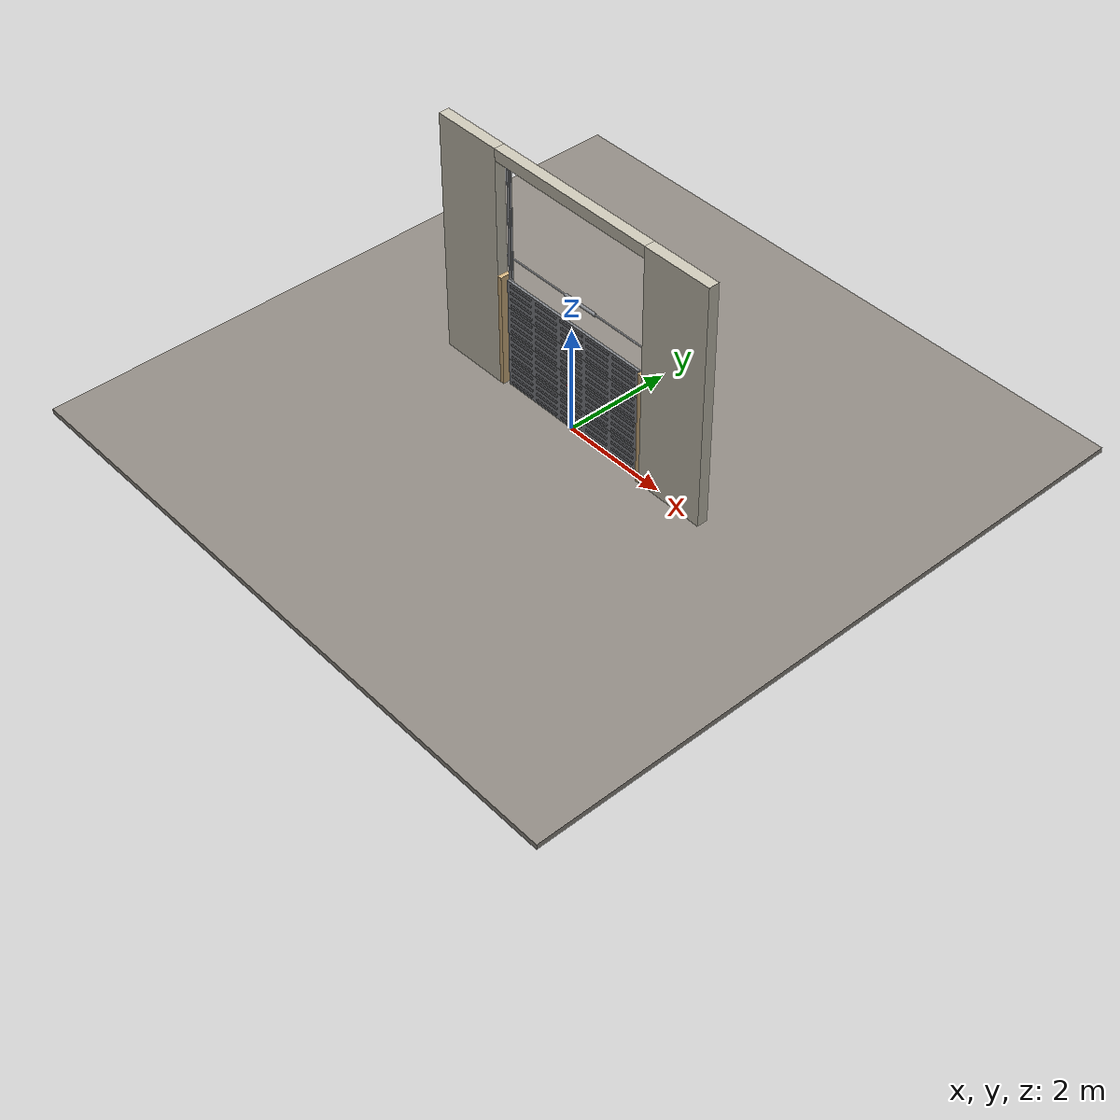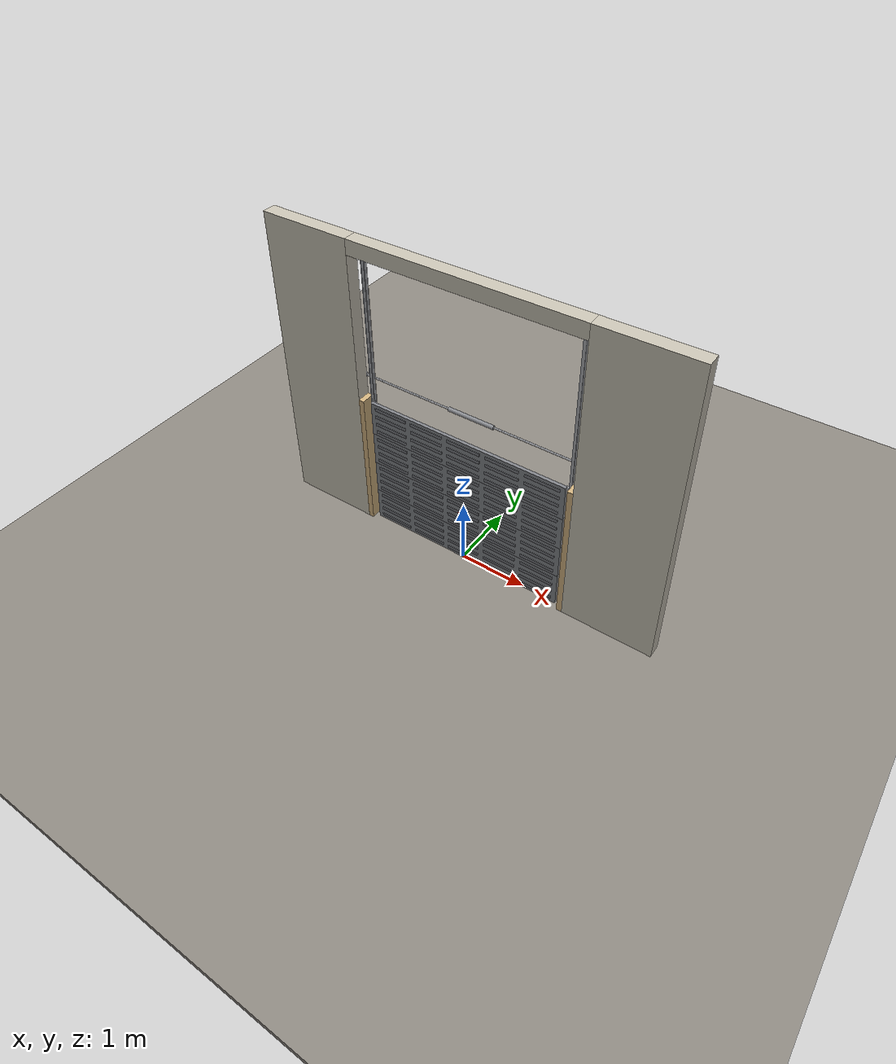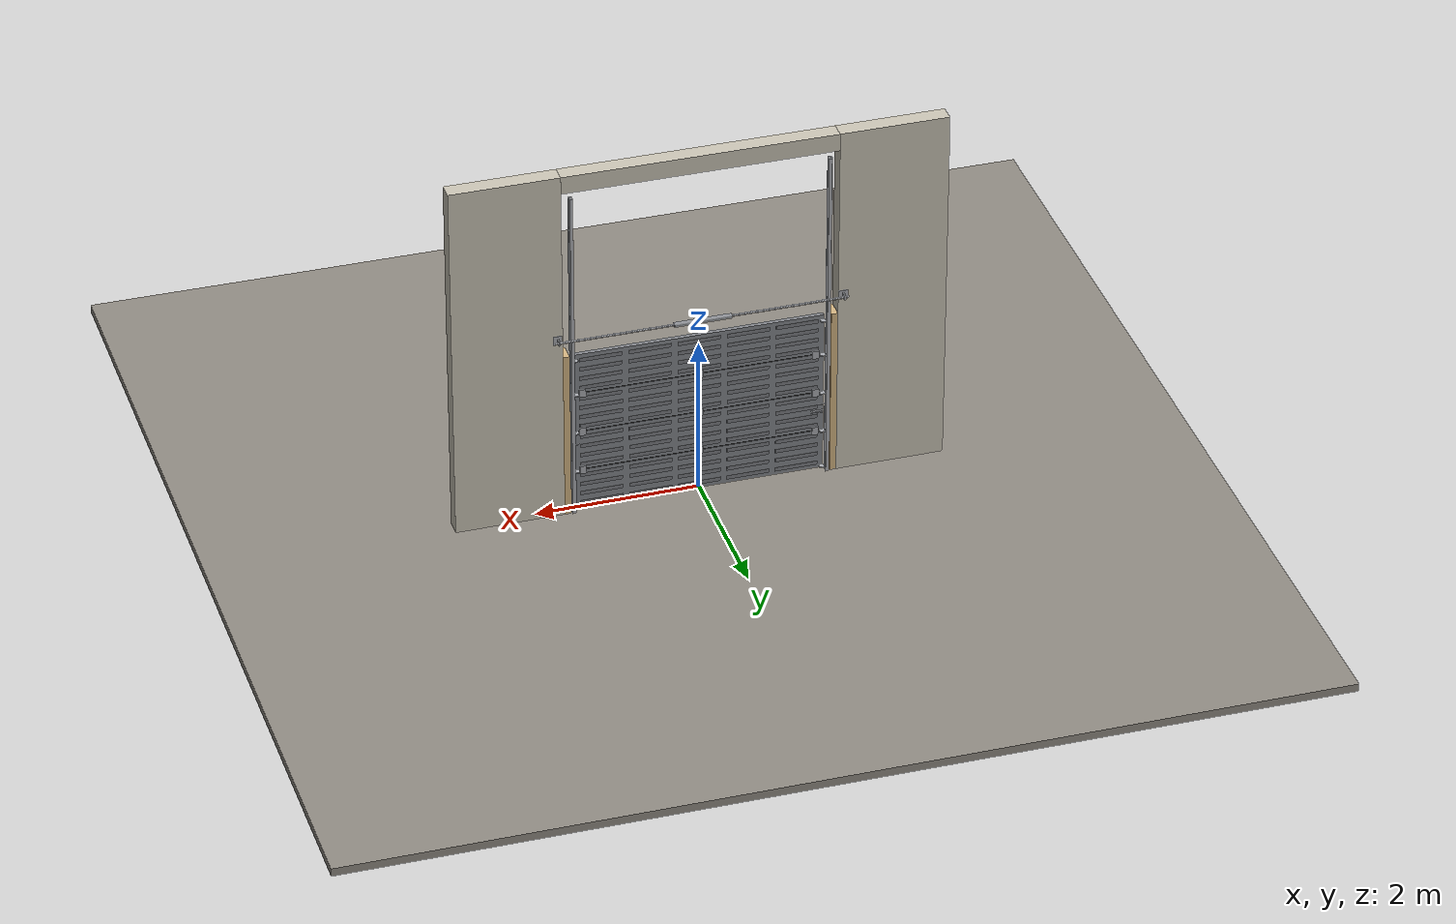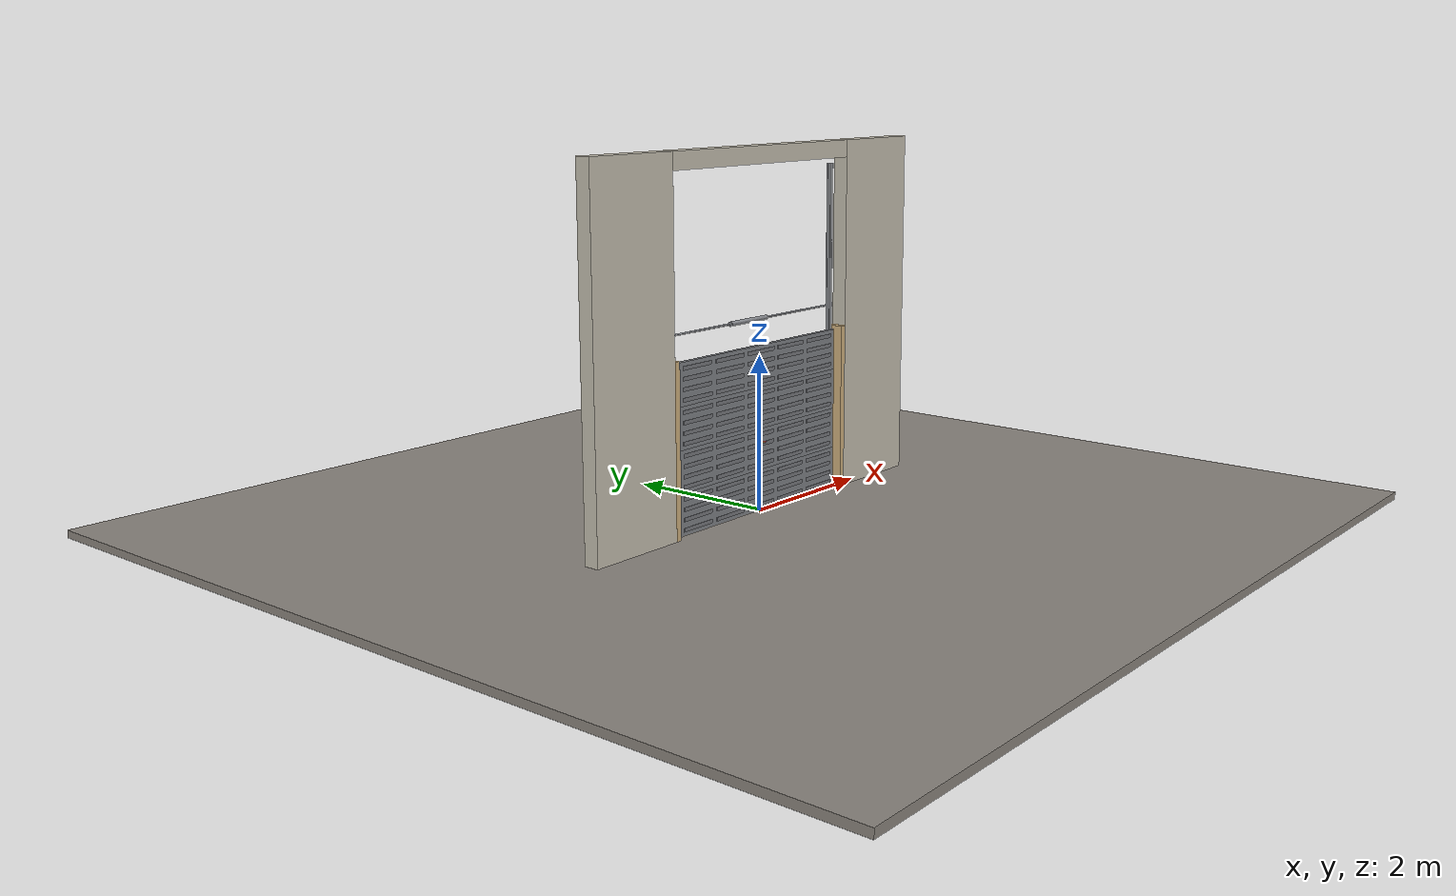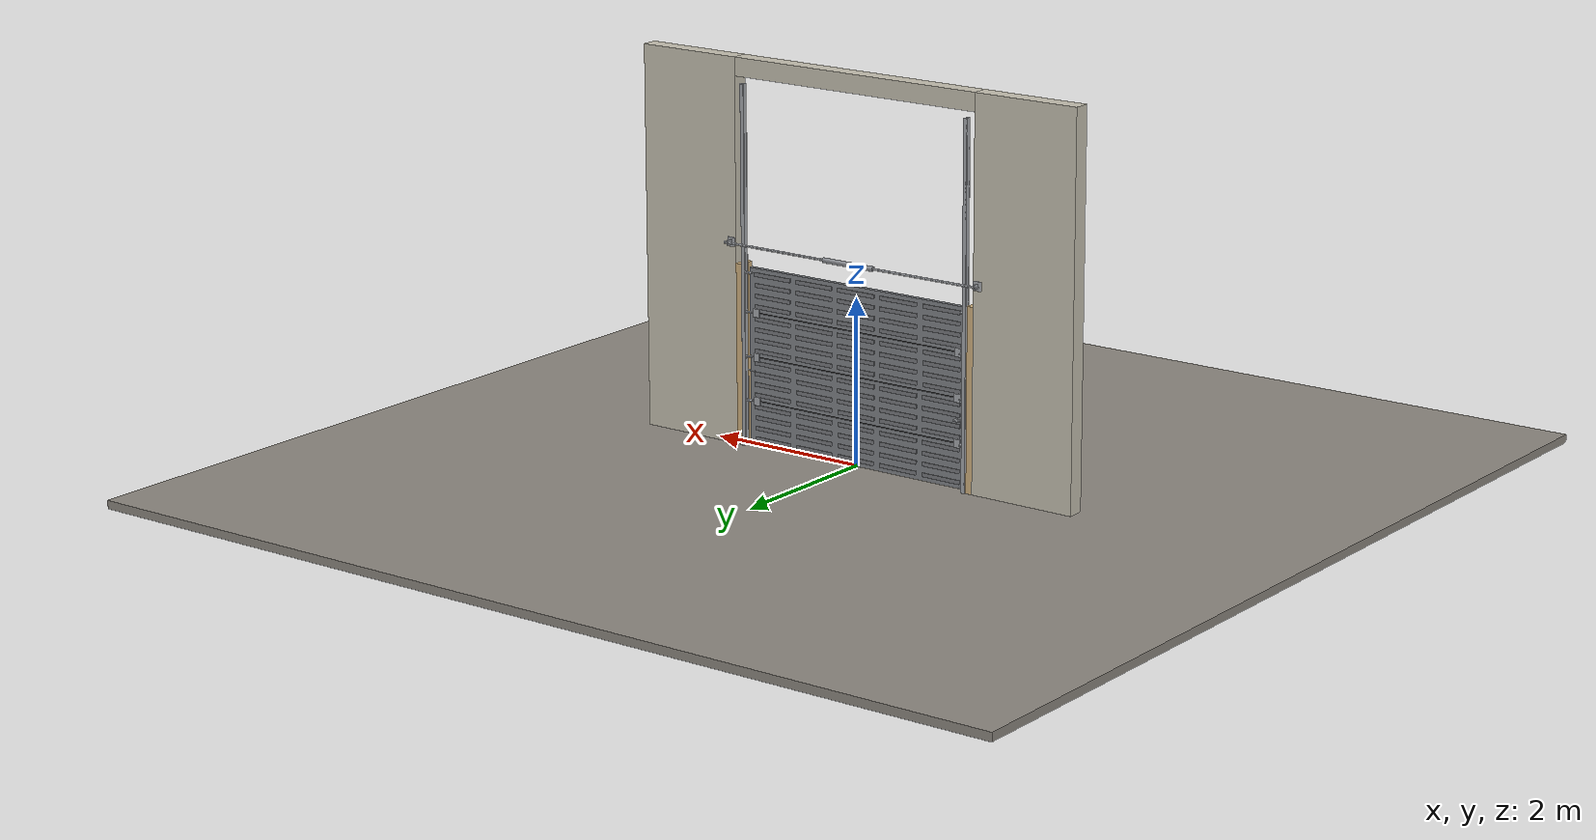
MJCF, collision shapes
<?xml version="1.0" ?>
<mujoco model="db0213_garage_sectional_full">
  <compiler angle="radian" meshdir="../../hardware" texturedir="../../textures" autolimits="true" inertiafromgeom="false"/>
  <option timestep="0.002" integrator="implicitfast" cone="elliptic" impratio="10" noslip_iterations="3">
    <flag multiccd="enable"/>
  </option>
  <size memory="16M"/>
  <default>
    <geom condim="4" solref="0.005 1" solimp="0.95 0.99 0.001"/>
    <joint solreflimit="0.005 1" solimplimit="0.95 0.99 0.001"/>
    <tendon solreflimit="0.005 1"/>
    <equality solref="0.002 1"/>
  </default>
  <visual>
    <headlight ambient="0.4 0.4 0.4" diffuse="0.7 0.7 0.7" specular="0.2 0.2 0.2"/>
    <quality shadowsize="4096"/>
    <map znear="0.01" zfar="60"/>
  </visual>
  <asset>
    <mesh name="lever_01c630149d" file="lever_01c630149d.obj"/>
    <material name="mat_floor" rgba="0.55 0.53 0.5 1" specular="0.2" shininess="0.15" reflectance="0"/>
    <material name="mat_wall" rgba="0.78 0.76 0.7 1" specular="0.2" shininess="0.1" reflectance="0"/>
    <material name="mat_frame" rgba="0.82 0.7 0.5 1" specular="0.2" shininess="0.45" reflectance="0"/>
    <material name="mat_track" rgba="0.65 0.66 0.68 1" specular="0.74" shininess="0.5" reflectance="0.36"/>
    <material name="mat_section_0" rgba="0.5 0.51 0.53 1" specular="0.23" shininess="0.63" reflectance="0.02"/>
    <material name="mat_section_0_panel" rgba="0.46 0.469 0.488 1" specular="0.23" shininess="0.63" reflectance="0.02"/>
    <material name="mat_section_1" rgba="0.5 0.51 0.53 1" specular="0.23" shininess="0.63" reflectance="0.02"/>
    <material name="mat_section_1_panel" rgba="0.46 0.469 0.488 1" specular="0.23" shininess="0.63" reflectance="0.02"/>
    <material name="mat_hinge_line" rgba="0.2 0.2 0.2 1" specular="0.2" shininess="0.3" reflectance="0"/>
    <material name="mat_section_2" rgba="0.5 0.51 0.53 1" specular="0.23" shininess="0.63" reflectance="0.02"/>
    <material name="mat_section_2_panel" rgba="0.46 0.469 0.488 1" specular="0.23" shininess="0.63" reflectance="0.02"/>
    <material name="mat_section_3" rgba="0.5 0.51 0.53 1" specular="0.23" shininess="0.63" reflectance="0.02"/>
    <material name="mat_section_3_panel" rgba="0.46 0.469 0.488 1" specular="0.23" shininess="0.63" reflectance="0.02"/>
    <material name="mat_spring" rgba="0.55 0.56 0.58 1" specular="0.8" shininess="0.55" reflectance="0.4"/>
    <material name="mat_op_black_matte_metal" rgba="0.05 0.05 0.05 1" specular="0.38" shininess="0.3" reflectance="0.12"/>
    <material name="mat_trim" rgba="0.85 0.66 0.3 1" specular="0.8" shininess="0.75" reflectance="0.4"/>
    <material name="mat_lockbar" rgba="0.65 0.66 0.68 1" specular="0.74" shininess="0.5" reflectance="0.36"/>
    <material name="mat_slidelock" rgba="0.65 0.66 0.68 1" specular="0.74" shininess="0.5" reflectance="0.36"/>
    <texture name="skybox" type="skybox" builtin="gradient" rgb1="0.6 0.7 0.85" rgb2="0.9 0.92 0.95" width="256" height="256"/>
  </asset>
  <worldbody>
    <light name="sun" pos="1.5 -2.5 4" dir="-0.3 0.5 -0.8" directional="true" diffuse="0.8 0.8 0.8" specular="0.3 0.3 0.3" castshadow="true"/>
    <light name="fill" pos="-1.5 2.5 3" dir="0.3 -0.5 -0.7" directional="true" diffuse="0.35 0.35 0.4" castshadow="false"/>
    <camera name="robot_view" pos="0 -3.53125 2.07875" xyaxes="1 0 0 0 0.26963 0.962964" fovy="52"/>
    <camera name="far_view" pos="0 3.53125 2.07875" xyaxes="-1 0 0 0 -0.26963 0.962964" fovy="52"/>
    <camera name="iso" pos="2.68375 -2.96625 2.64375" xyaxes="0.741536 0.670913 0 -0.242917 0.268487 0.932151" fovy="46"/>
    <camera name="detail_handle" pos="0.2115 -1.165 1.25" xyaxes="0.975133 0.221621 0 -0.065674 0.288965 0.955084" fovy="38"/>
    <geom name="floor" type="box" size="6 6 0.05" pos="0 0 -0.05" material="mat_floor" group="0" contype="1" conaffinity="1" friction="0.8 0.005 0.0001" density="2400"/>
    <geom name="wall_left" type="box" size="0.665 0.1 2.305" pos="-2.335 0 2.305" material="mat_wall" group="0" contype="1" conaffinity="1" friction="0.6 0.005 0.0001" density="800"/>
    <geom name="wall_right" type="box" size="0.665 0.1 2.305" pos="2.335 0 2.305" material="mat_wall" group="0" contype="1" conaffinity="1" friction="0.6 0.005 0.0001" density="800"/>
    <geom name="wall_header" type="box" size="1.67 0.1 0.11" pos="0 0 4.5" material="mat_wall" group="0" contype="1" conaffinity="1" friction="0.6 0.005 0.0001" density="800"/>
    <geom name="garage_jamb_l" type="box" size="0.04 0.1 1.09" pos="-1.63 0 1.09" material="mat_frame" group="0" contype="1" conaffinity="1" friction="0.6 0.005 0.0001" density="400"/>
    <geom name="garage_jamb_r" type="box" size="0.04 0.1 1.09" pos="1.63 0 1.09" material="mat_frame" group="0" contype="1" conaffinity="1" friction="0.6 0.005 0.0001" density="400"/>
    <geom name="track_l" type="box" size="0.004 0.033 2.155" pos="-1.575 0.085 2.155" material="mat_track" group="0" contype="1" conaffinity="1" friction="0.6 0.005 0.0001" density="7850"/>
    <geom name="track_l_flange_n" type="box" size="0.022 0.004 2.155" pos="-1.557 0.056 2.155" material="mat_track" group="0" contype="1" conaffinity="1" friction="0.6 0.005 0.0001" density="7850"/>
    <geom name="track_l_flange_p" type="box" size="0.022 0.004 2.155" pos="-1.557 0.114 2.155" material="mat_track" group="0" contype="1" conaffinity="1" friction="0.6 0.005 0.0001" density="7850"/>
    <geom name="track_r" type="box" size="0.004 0.033 2.155" pos="1.575 0.085 2.155" material="mat_track" group="0" contype="1" conaffinity="1" friction="0.6 0.005 0.0001" density="7850"/>
    <geom name="track_r_flange_n" type="box" size="0.022 0.004 2.155" pos="1.557 0.056 2.155" material="mat_track" group="0" contype="1" conaffinity="1" friction="0.6 0.005 0.0001" density="7850"/>
    <geom name="track_r_flange_p" type="box" size="0.022 0.004 2.155" pos="1.557 0.114 2.155" material="mat_track" group="0" contype="1" conaffinity="1" friction="0.6 0.005 0.0001" density="7850"/>
    <geom name="torsion_shaft" type="cylinder" size="0.013 1.78" pos="0 0.17 2.43" quat="0.707107 0 0.707107 0" material="mat_track" group="0" contype="1" conaffinity="1" friction="0.6 0.005 0.0001" density="7850"/>
    <geom name="torsion_spring" type="cylinder" size="0.03 0.35" pos="0 0.17 2.43" quat="0.707107 0 0.707107 0" material="mat_spring" group="1" contype="0" conaffinity="0" density="7850"/>
    <geom name="torsion_bearing_plate_l" type="box" size="0.055 0.004 0.055" pos="-1.73 0.104 2.43" material="mat_track" group="1" contype="0" conaffinity="0" density="7850"/>
    <geom name="torsion_bearing_arm_l" type="box" size="0.008 0.049 0.03" pos="-1.73 0.139 2.43" material="mat_track" group="1" contype="0" conaffinity="0" density="7850"/>
    <geom name="torsion_bearing_plate_r" type="box" size="0.055 0.004 0.055" pos="1.73 0.104 2.43" material="mat_track" group="1" contype="0" conaffinity="0" density="7850"/>
    <geom name="torsion_bearing_arm_r" type="box" size="0.008 0.049 0.03" pos="1.73 0.139 2.43" material="mat_track" group="1" contype="0" conaffinity="0" density="7850"/>
    <geom name="slide_lock_keeper_leg_n" type="box" size="0.007 0.0025 0.0155" pos="-1.57 0.0365 0.82025" quat="0 0 -0.707107 0.707107" material="mat_track" group="0" contype="1" conaffinity="1" friction="0.6 0.005 0.0001" density="7800"/>
    <geom name="slide_lock_keeper_leg_p" type="box" size="0.007 0.0025 0.0155" pos="-1.57 0.0365 0.79725" quat="0 0 -0.707107 0.707107" material="mat_track" group="0" contype="1" conaffinity="1" friction="0.6 0.005 0.0001" density="7800"/>
    <geom name="slide_lock_keeper_bridge" type="box" size="0.007 0.014 0.0025" pos="-1.57 0.0235 0.80875" quat="0 0 -0.707107 0.707107" material="mat_track" group="0" contype="1" conaffinity="1" friction="0.6 0.005 0.0001" density="7800"/>
    <geom name="slide_lock_keeper_base" type="box" size="0.015 0.02 0.001" pos="-1.57 0.051 0.80875" quat="0 0 -0.707107 0.707107" material="mat_track" group="1" contype="0" conaffinity="0" density="7800"/>
    <site name="approach_point" pos="0 -2 0" quat="1 0 0 0" size="0.05" rgba="0.2 0.9 0.2 0.5" group="4"/>
    <site name="goal_point" pos="0 2 0" quat="1 0 0 0" size="0.05" rgba="0.2 0.9 0.2 0.5" group="4"/>
    <site name="door_plane_center" pos="0 0 1.09" quat="1 0 0 0" size="0.02" rgba="0.2 0.9 0.2 0.5" group="4"/>
    <body name="door" pos="0 0 0">
      <inertial pos="-0.001957 0.008479 1.074241" mass="86.503393" quat="0.707138 -0.707075 -0.000302 -0.000336" diaginertia="31.835257014 81.623531241 113.355929682"/>
      <joint name="door_slide" type="slide" axis="0 0 1" limited="true" range="0 2.08" damping="6.358421" frictionloss="22.225584" armature="0.5"/>
      <geom name="section_0_slab" type="box" size="1.525 0.025 0.26625" pos="0 0 0.27625" material="mat_section_0" group="0" contype="1" conaffinity="1" friction="0.4 0.005 0.0001" density="1"/>
      <geom name="section_0_panel_0_n" type="box" size="0.259 0.003 0.024062" pos="-1.196 -0.028 0.084062" material="mat_section_0_panel" group="1" contype="0" conaffinity="0" density="1"/>
      <geom name="section_0_panel_0_p" type="box" size="0.259 0.003 0.024062" pos="-1.196 0.028 0.084062" material="mat_section_0_panel" group="1" contype="0" conaffinity="0" density="1"/>
      <geom name="section_0_panel_1_n" type="box" size="0.259 0.003 0.024062" pos="-0.598 -0.028 0.084062" material="mat_section_0_panel" group="1" contype="0" conaffinity="0" density="1"/>
      <geom name="section_0_panel_1_p" type="box" size="0.259 0.003 0.024062" pos="-0.598 0.028 0.084062" material="mat_section_0_panel" group="1" contype="0" conaffinity="0" density="1"/>
      <geom name="section_0_panel_2_n" type="box" size="0.259 0.003 0.024062" pos="0 -0.028 0.084062" material="mat_section_0_panel" group="1" contype="0" conaffinity="0" density="1"/>
      <geom name="section_0_panel_2_p" type="box" size="0.259 0.003 0.024062" pos="0 0.028 0.084062" material="mat_section_0_panel" group="1" contype="0" conaffinity="0" density="1"/>
      <geom name="section_0_panel_3_n" type="box" size="0.259 0.003 0.024062" pos="0.598 -0.028 0.084062" material="mat_section_0_panel" group="1" contype="0" conaffinity="0" density="1"/>
      <geom name="section_0_panel_3_p" type="box" size="0.259 0.003 0.024062" pos="0.598 0.028 0.084062" material="mat_section_0_panel" group="1" contype="0" conaffinity="0" density="1"/>
      <geom name="section_0_panel_4_n" type="box" size="0.259 0.003 0.024062" pos="1.196 -0.028 0.084062" material="mat_section_0_panel" group="1" contype="0" conaffinity="0" density="1"/>
      <geom name="section_0_panel_4_p" type="box" size="0.259 0.003 0.024062" pos="1.196 0.028 0.084062" material="mat_section_0_panel" group="1" contype="0" conaffinity="0" density="1"/>
      <geom name="section_0_panel_5_n" type="box" size="0.259 0.003 0.024062" pos="-1.196 -0.028 0.212188" material="mat_section_0_panel" group="1" contype="0" conaffinity="0" density="1"/>
      <geom name="section_0_panel_5_p" type="box" size="0.259 0.003 0.024062" pos="-1.196 0.028 0.212188" material="mat_section_0_panel" group="1" contype="0" conaffinity="0" density="1"/>
      <geom name="section_0_panel_6_n" type="box" size="0.259 0.003 0.024062" pos="-0.598 -0.028 0.212188" material="mat_section_0_panel" group="1" contype="0" conaffinity="0" density="1"/>
      <geom name="section_0_panel_6_p" type="box" size="0.259 0.003 0.024062" pos="-0.598 0.028 0.212188" material="mat_section_0_panel" group="1" contype="0" conaffinity="0" density="1"/>
      <geom name="section_0_panel_7_n" type="box" size="0.259 0.003 0.024062" pos="0 -0.028 0.212188" material="mat_section_0_panel" group="1" contype="0" conaffinity="0" density="1"/>
      <geom name="section_0_panel_7_p" type="box" size="0.259 0.003 0.024062" pos="0 0.028 0.212188" material="mat_section_0_panel" group="1" contype="0" conaffinity="0" density="1"/>
      <geom name="section_0_panel_8_n" type="box" size="0.259 0.003 0.024062" pos="0.598 -0.028 0.212188" material="mat_section_0_panel" group="1" contype="0" conaffinity="0" density="1"/>
      <geom name="section_0_panel_8_p" type="box" size="0.259 0.003 0.024062" pos="0.598 0.028 0.212188" material="mat_section_0_panel" group="1" contype="0" conaffinity="0" density="1"/>
      <geom name="section_0_panel_9_n" type="box" size="0.259 0.003 0.024062" pos="1.196 -0.028 0.212188" material="mat_section_0_panel" group="1" contype="0" conaffinity="0" density="1"/>
      <geom name="section_0_panel_9_p" type="box" size="0.259 0.003 0.024062" pos="1.196 0.028 0.212188" material="mat_section_0_panel" group="1" contype="0" conaffinity="0" density="1"/>
      <geom name="section_0_panel_10_n" type="box" size="0.259 0.003 0.024062" pos="-1.196 -0.028 0.340313" material="mat_section_0_panel" group="1" contype="0" conaffinity="0" density="1"/>
      <geom name="section_0_panel_10_p" type="box" size="0.259 0.003 0.024062" pos="-1.196 0.028 0.340313" material="mat_section_0_panel" group="1" contype="0" conaffinity="0" density="1"/>
      <geom name="section_0_panel_11_n" type="box" size="0.259 0.003 0.024062" pos="-0.598 -0.028 0.340313" material="mat_section_0_panel" group="1" contype="0" conaffinity="0" density="1"/>
      <geom name="section_0_panel_11_p" type="box" size="0.259 0.003 0.024062" pos="-0.598 0.028 0.340313" material="mat_section_0_panel" group="1" contype="0" conaffinity="0" density="1"/>
      <geom name="section_0_panel_12_n" type="box" size="0.259 0.003 0.024062" pos="0 -0.028 0.340313" material="mat_section_0_panel" group="1" contype="0" conaffinity="0" density="1"/>
      <geom name="section_0_panel_12_p" type="box" size="0.259 0.003 0.024062" pos="0 0.028 0.340313" material="mat_section_0_panel" group="1" contype="0" conaffinity="0" density="1"/>
      <geom name="section_0_panel_13_n" type="box" size="0.259 0.003 0.024062" pos="0.598 -0.028 0.340313" material="mat_section_0_panel" group="1" contype="0" conaffinity="0" density="1"/>
      <geom name="section_0_panel_13_p" type="box" size="0.259 0.003 0.024062" pos="0.598 0.028 0.340313" material="mat_section_0_panel" group="1" contype="0" conaffinity="0" density="1"/>
      <geom name="section_0_panel_14_n" type="box" size="0.259 0.003 0.024062" pos="1.196 -0.028 0.340313" material="mat_section_0_panel" group="1" contype="0" conaffinity="0" density="1"/>
      <geom name="section_0_panel_14_p" type="box" size="0.259 0.003 0.024062" pos="1.196 0.028 0.340313" material="mat_section_0_panel" group="1" contype="0" conaffinity="0" density="1"/>
      <geom name="section_0_panel_15_n" type="box" size="0.259 0.003 0.024062" pos="-1.196 -0.028 0.468437" material="mat_section_0_panel" group="1" contype="0" conaffinity="0" density="1"/>
      <geom name="section_0_panel_15_p" type="box" size="0.259 0.003 0.024062" pos="-1.196 0.028 0.468437" material="mat_section_0_panel" group="1" contype="0" conaffinity="0" density="1"/>
      <geom name="section_0_panel_16_n" type="box" size="0.259 0.003 0.024062" pos="-0.598 -0.028 0.468437" material="mat_section_0_panel" group="1" contype="0" conaffinity="0" density="1"/>
      <geom name="section_0_panel_16_p" type="box" size="0.259 0.003 0.024062" pos="-0.598 0.028 0.468437" material="mat_section_0_panel" group="1" contype="0" conaffinity="0" density="1"/>
      <geom name="section_0_panel_17_n" type="box" size="0.259 0.003 0.024062" pos="0 -0.028 0.468437" material="mat_section_0_panel" group="1" contype="0" conaffinity="0" density="1"/>
      <geom name="section_0_panel_17_p" type="box" size="0.259 0.003 0.024062" pos="0 0.028 0.468437" material="mat_section_0_panel" group="1" contype="0" conaffinity="0" density="1"/>
      <geom name="section_0_panel_18_n" type="box" size="0.259 0.003 0.024062" pos="0.598 -0.028 0.468437" material="mat_section_0_panel" group="1" contype="0" conaffinity="0" density="1"/>
      <geom name="section_0_panel_18_p" type="box" size="0.259 0.003 0.024062" pos="0.598 0.028 0.468437" material="mat_section_0_panel" group="1" contype="0" conaffinity="0" density="1"/>
      <geom name="section_0_panel_19_n" type="box" size="0.259 0.003 0.024062" pos="1.196 -0.028 0.468437" material="mat_section_0_panel" group="1" contype="0" conaffinity="0" density="1"/>
      <geom name="section_0_panel_19_p" type="box" size="0.259 0.003 0.024062" pos="1.196 0.028 0.468437" material="mat_section_0_panel" group="1" contype="0" conaffinity="0" density="1"/>
      <geom name="section_1_slab" type="box" size="1.525 0.025 0.26625" pos="0 0 0.80875" material="mat_section_1" group="0" contype="1" conaffinity="1" friction="0.4 0.005 0.0001" density="1"/>
      <geom name="section_1_panel_0_n" type="box" size="0.259 0.003 0.024062" pos="-1.196 -0.028 0.616563" material="mat_section_1_panel" group="1" contype="0" conaffinity="0" density="1"/>
      <geom name="section_1_panel_0_p" type="box" size="0.259 0.003 0.024062" pos="-1.196 0.028 0.616563" material="mat_section_1_panel" group="1" contype="0" conaffinity="0" density="1"/>
      <geom name="section_1_panel_1_n" type="box" size="0.259 0.003 0.024062" pos="-0.598 -0.028 0.616563" material="mat_section_1_panel" group="1" contype="0" conaffinity="0" density="1"/>
      <geom name="section_1_panel_1_p" type="box" size="0.259 0.003 0.024062" pos="-0.598 0.028 0.616563" material="mat_section_1_panel" group="1" contype="0" conaffinity="0" density="1"/>
      <geom name="section_1_panel_2_n" type="box" size="0.259 0.003 0.024062" pos="0 -0.028 0.616563" material="mat_section_1_panel" group="1" contype="0" conaffinity="0" density="1"/>
      <geom name="section_1_panel_2_p" type="box" size="0.259 0.003 0.024062" pos="0 0.028 0.616563" material="mat_section_1_panel" group="1" contype="0" conaffinity="0" density="1"/>
      <geom name="section_1_panel_3_n" type="box" size="0.259 0.003 0.024062" pos="0.598 -0.028 0.616563" material="mat_section_1_panel" group="1" contype="0" conaffinity="0" density="1"/>
      <geom name="section_1_panel_3_p" type="box" size="0.259 0.003 0.024062" pos="0.598 0.028 0.616563" material="mat_section_1_panel" group="1" contype="0" conaffinity="0" density="1"/>
      <geom name="section_1_panel_4_n" type="box" size="0.259 0.003 0.024062" pos="1.196 -0.028 0.616563" material="mat_section_1_panel" group="1" contype="0" conaffinity="0" density="1"/>
      <geom name="section_1_panel_4_p" type="box" size="0.259 0.003 0.024062" pos="1.196 0.028 0.616563" material="mat_section_1_panel" group="1" contype="0" conaffinity="0" density="1"/>
      <geom name="section_1_panel_5_n" type="box" size="0.259 0.003 0.024062" pos="-1.196 -0.028 0.744687" material="mat_section_1_panel" group="1" contype="0" conaffinity="0" density="1"/>
      <geom name="section_1_panel_5_p" type="box" size="0.259 0.003 0.024062" pos="-1.196 0.028 0.744687" material="mat_section_1_panel" group="1" contype="0" conaffinity="0" density="1"/>
      <geom name="section_1_panel_6_n" type="box" size="0.259 0.003 0.024062" pos="-0.598 -0.028 0.744687" material="mat_section_1_panel" group="1" contype="0" conaffinity="0" density="1"/>
      <geom name="section_1_panel_6_p" type="box" size="0.259 0.003 0.024062" pos="-0.598 0.028 0.744687" material="mat_section_1_panel" group="1" contype="0" conaffinity="0" density="1"/>
      <geom name="section_1_panel_7_n" type="box" size="0.259 0.003 0.024062" pos="0 -0.028 0.744687" material="mat_section_1_panel" group="1" contype="0" conaffinity="0" density="1"/>
      <geom name="section_1_panel_7_p" type="box" size="0.259 0.003 0.024062" pos="0 0.028 0.744687" material="mat_section_1_panel" group="1" contype="0" conaffinity="0" density="1"/>
      <geom name="section_1_panel_8_n" type="box" size="0.259 0.003 0.024062" pos="0.598 -0.028 0.744687" material="mat_section_1_panel" group="1" contype="0" conaffinity="0" density="1"/>
      <geom name="section_1_panel_8_p" type="box" size="0.259 0.003 0.024062" pos="0.598 0.028 0.744687" material="mat_section_1_panel" group="1" contype="0" conaffinity="0" density="1"/>
      <geom name="section_1_panel_9_n" type="box" size="0.259 0.003 0.024062" pos="1.196 -0.028 0.744687" material="mat_section_1_panel" group="1" contype="0" conaffinity="0" density="1"/>
      <geom name="section_1_panel_9_p" type="box" size="0.259 0.003 0.024062" pos="1.196 0.028 0.744687" material="mat_section_1_panel" group="1" contype="0" conaffinity="0" density="1"/>
      <geom name="section_1_panel_10_n" type="box" size="0.259 0.003 0.024062" pos="-1.196 -0.028 0.872812" material="mat_section_1_panel" group="1" contype="0" conaffinity="0" density="1"/>
      <geom name="section_1_panel_10_p" type="box" size="0.259 0.003 0.024062" pos="-1.196 0.028 0.872812" material="mat_section_1_panel" group="1" contype="0" conaffinity="0" density="1"/>
      <geom name="section_1_panel_11_n" type="box" size="0.259 0.003 0.024062" pos="-0.598 -0.028 0.872812" material="mat_section_1_panel" group="1" contype="0" conaffinity="0" density="1"/>
      <geom name="section_1_panel_11_p" type="box" size="0.259 0.003 0.024062" pos="-0.598 0.028 0.872812" material="mat_section_1_panel" group="1" contype="0" conaffinity="0" density="1"/>
      <geom name="section_1_panel_12_n" type="box" size="0.259 0.003 0.024062" pos="0 -0.028 0.872812" material="mat_section_1_panel" group="1" contype="0" conaffinity="0" density="1"/>
      <geom name="section_1_panel_12_p" type="box" size="0.259 0.003 0.024062" pos="0 0.028 0.872812" material="mat_section_1_panel" group="1" contype="0" conaffinity="0" density="1"/>
      <geom name="section_1_panel_13_n" type="box" size="0.259 0.003 0.024062" pos="0.598 -0.028 0.872812" material="mat_section_1_panel" group="1" contype="0" conaffinity="0" density="1"/>
      <geom name="section_1_panel_13_p" type="box" size="0.259 0.003 0.024062" pos="0.598 0.028 0.872812" material="mat_section_1_panel" group="1" contype="0" conaffinity="0" density="1"/>
      <geom name="section_1_panel_14_n" type="box" size="0.259 0.003 0.024062" pos="1.196 -0.028 0.872812" material="mat_section_1_panel" group="1" contype="0" conaffinity="0" density="1"/>
      <geom name="section_1_panel_14_p" type="box" size="0.259 0.003 0.024062" pos="1.196 0.028 0.872812" material="mat_section_1_panel" group="1" contype="0" conaffinity="0" density="1"/>
      <geom name="section_1_panel_15_n" type="box" size="0.259 0.003 0.024062" pos="-1.196 -0.028 1.000937" material="mat_section_1_panel" group="1" contype="0" conaffinity="0" density="1"/>
      <geom name="section_1_panel_15_p" type="box" size="0.259 0.003 0.024062" pos="-1.196 0.028 1.000937" material="mat_section_1_panel" group="1" contype="0" conaffinity="0" density="1"/>
      <geom name="section_1_panel_16_n" type="box" size="0.259 0.003 0.024062" pos="-0.598 -0.028 1.000937" material="mat_section_1_panel" group="1" contype="0" conaffinity="0" density="1"/>
      <geom name="section_1_panel_16_p" type="box" size="0.259 0.003 0.024062" pos="-0.598 0.028 1.000937" material="mat_section_1_panel" group="1" contype="0" conaffinity="0" density="1"/>
      <geom name="section_1_panel_17_n" type="box" size="0.259 0.003 0.024062" pos="0 -0.028 1.000937" material="mat_section_1_panel" group="1" contype="0" conaffinity="0" density="1"/>
      <geom name="section_1_panel_17_p" type="box" size="0.259 0.003 0.024062" pos="0 0.028 1.000937" material="mat_section_1_panel" group="1" contype="0" conaffinity="0" density="1"/>
      <geom name="section_1_panel_18_n" type="box" size="0.259 0.003 0.024062" pos="0.598 -0.028 1.000937" material="mat_section_1_panel" group="1" contype="0" conaffinity="0" density="1"/>
      <geom name="section_1_panel_18_p" type="box" size="0.259 0.003 0.024062" pos="0.598 0.028 1.000937" material="mat_section_1_panel" group="1" contype="0" conaffinity="0" density="1"/>
      <geom name="section_1_panel_19_n" type="box" size="0.259 0.003 0.024062" pos="1.196 -0.028 1.000937" material="mat_section_1_panel" group="1" contype="0" conaffinity="0" density="1"/>
      <geom name="section_1_panel_19_p" type="box" size="0.259 0.003 0.024062" pos="1.196 0.028 1.000937" material="mat_section_1_panel" group="1" contype="0" conaffinity="0" density="1"/>
      <geom name="section_hinge_line_1" type="box" size="1.505 0.001 0.004" pos="0 0.026 0.5425" material="mat_hinge_line" group="1" contype="0" conaffinity="0" density="1"/>
      <geom name="section_hinge_1_162" type="box" size="0.04 0.01 0.05" pos="-1.425 0.035 0.5425" material="mat_track" group="1" contype="0" conaffinity="0" density="7850"/>
      <geom name="section_hinge_1_305" type="box" size="0.04 0.01 0.05" pos="0 0.035 0.5425" material="mat_track" group="1" contype="0" conaffinity="0" density="7850"/>
      <geom name="section_hinge_1_447" type="box" size="0.04 0.01 0.05" pos="1.425 0.035 0.5425" material="mat_track" group="1" contype="0" conaffinity="0" density="7850"/>
      <geom name="section_2_slab" type="box" size="1.525 0.025 0.26625" pos="0 0 1.34125" material="mat_section_2" group="0" contype="1" conaffinity="1" friction="0.4 0.005 0.0001" density="1"/>
      <geom name="section_2_panel_0_n" type="box" size="0.259 0.003 0.024062" pos="-1.196 -0.028 1.149062" material="mat_section_2_panel" group="1" contype="0" conaffinity="0" density="1"/>
      <geom name="section_2_panel_0_p" type="box" size="0.259 0.003 0.024062" pos="-1.196 0.028 1.149062" material="mat_section_2_panel" group="1" contype="0" conaffinity="0" density="1"/>
      <geom name="section_2_panel_1_n" type="box" size="0.259 0.003 0.024062" pos="-0.598 -0.028 1.149062" material="mat_section_2_panel" group="1" contype="0" conaffinity="0" density="1"/>
      <geom name="section_2_panel_1_p" type="box" size="0.259 0.003 0.024062" pos="-0.598 0.028 1.149062" material="mat_section_2_panel" group="1" contype="0" conaffinity="0" density="1"/>
      <geom name="section_2_panel_2_n" type="box" size="0.259 0.003 0.024062" pos="0 -0.028 1.149062" material="mat_section_2_panel" group="1" contype="0" conaffinity="0" density="1"/>
      <geom name="section_2_panel_2_p" type="box" size="0.259 0.003 0.024062" pos="0 0.028 1.149062" material="mat_section_2_panel" group="1" contype="0" conaffinity="0" density="1"/>
      <geom name="section_2_panel_3_n" type="box" size="0.259 0.003 0.024062" pos="0.598 -0.028 1.149062" material="mat_section_2_panel" group="1" contype="0" conaffinity="0" density="1"/>
      <geom name="section_2_panel_3_p" type="box" size="0.259 0.003 0.024062" pos="0.598 0.028 1.149062" material="mat_section_2_panel" group="1" contype="0" conaffinity="0" density="1"/>
      <geom name="section_2_panel_4_n" type="box" size="0.259 0.003 0.024062" pos="1.196 -0.028 1.149062" material="mat_section_2_panel" group="1" contype="0" conaffinity="0" density="1"/>
      <geom name="section_2_panel_4_p" type="box" size="0.259 0.003 0.024062" pos="1.196 0.028 1.149062" material="mat_section_2_panel" group="1" contype="0" conaffinity="0" density="1"/>
      <geom name="section_2_panel_5_n" type="box" size="0.259 0.003 0.024062" pos="-1.196 -0.028 1.277187" material="mat_section_2_panel" group="1" contype="0" conaffinity="0" density="1"/>
      <geom name="section_2_panel_5_p" type="box" size="0.259 0.003 0.024062" pos="-1.196 0.028 1.277187" material="mat_section_2_panel" group="1" contype="0" conaffinity="0" density="1"/>
      <geom name="section_2_panel_6_n" type="box" size="0.259 0.003 0.024062" pos="-0.598 -0.028 1.277187" material="mat_section_2_panel" group="1" contype="0" conaffinity="0" density="1"/>
      <geom name="section_2_panel_6_p" type="box" size="0.259 0.003 0.024062" pos="-0.598 0.028 1.277187" material="mat_section_2_panel" group="1" contype="0" conaffinity="0" density="1"/>
      <geom name="section_2_panel_7_n" type="box" size="0.259 0.003 0.024062" pos="0 -0.028 1.277187" material="mat_section_2_panel" group="1" contype="0" conaffinity="0" density="1"/>
      <geom name="section_2_panel_7_p" type="box" size="0.259 0.003 0.024062" pos="0 0.028 1.277187" material="mat_section_2_panel" group="1" contype="0" conaffinity="0" density="1"/>
      <geom name="section_2_panel_8_n" type="box" size="0.259 0.003 0.024062" pos="0.598 -0.028 1.277187" material="mat_section_2_panel" group="1" contype="0" conaffinity="0" density="1"/>
      <geom name="section_2_panel_8_p" type="box" size="0.259 0.003 0.024062" pos="0.598 0.028 1.277187" material="mat_section_2_panel" group="1" contype="0" conaffinity="0" density="1"/>
      <geom name="section_2_panel_9_n" type="box" size="0.259 0.003 0.024062" pos="1.196 -0.028 1.277187" material="mat_section_2_panel" group="1" contype="0" conaffinity="0" density="1"/>
      <geom name="section_2_panel_9_p" type="box" size="0.259 0.003 0.024062" pos="1.196 0.028 1.277187" material="mat_section_2_panel" group="1" contype="0" conaffinity="0" density="1"/>
      <geom name="section_2_panel_10_n" type="box" size="0.259 0.003 0.024062" pos="-1.196 -0.028 1.405312" material="mat_section_2_panel" group="1" contype="0" conaffinity="0" density="1"/>
      <geom name="section_2_panel_10_p" type="box" size="0.259 0.003 0.024062" pos="-1.196 0.028 1.405312" material="mat_section_2_panel" group="1" contype="0" conaffinity="0" density="1"/>
      <geom name="section_2_panel_11_n" type="box" size="0.259 0.003 0.024062" pos="-0.598 -0.028 1.405312" material="mat_section_2_panel" group="1" contype="0" conaffinity="0" density="1"/>
      <geom name="section_2_panel_11_p" type="box" size="0.259 0.003 0.024062" pos="-0.598 0.028 1.405312" material="mat_section_2_panel" group="1" contype="0" conaffinity="0" density="1"/>
      <geom name="section_2_panel_12_n" type="box" size="0.259 0.003 0.024062" pos="0 -0.028 1.405312" material="mat_section_2_panel" group="1" contype="0" conaffinity="0" density="1"/>
      <geom name="section_2_panel_12_p" type="box" size="0.259 0.003 0.024062" pos="0 0.028 1.405312" material="mat_section_2_panel" group="1" contype="0" conaffinity="0" density="1"/>
      <geom name="section_2_panel_13_n" type="box" size="0.259 0.003 0.024062" pos="0.598 -0.028 1.405312" material="mat_section_2_panel" group="1" contype="0" conaffinity="0" density="1"/>
      <geom name="section_2_panel_13_p" type="box" size="0.259 0.003 0.024062" pos="0.598 0.028 1.405312" material="mat_section_2_panel" group="1" contype="0" conaffinity="0" density="1"/>
      <geom name="section_2_panel_14_n" type="box" size="0.259 0.003 0.024062" pos="1.196 -0.028 1.405312" material="mat_section_2_panel" group="1" contype="0" conaffinity="0" density="1"/>
      <geom name="section_2_panel_14_p" type="box" size="0.259 0.003 0.024062" pos="1.196 0.028 1.405312" material="mat_section_2_panel" group="1" contype="0" conaffinity="0" density="1"/>
      <geom name="section_2_panel_15_n" type="box" size="0.259 0.003 0.024062" pos="-1.196 -0.028 1.533437" material="mat_section_2_panel" group="1" contype="0" conaffinity="0" density="1"/>
      <geom name="section_2_panel_15_p" type="box" size="0.259 0.003 0.024062" pos="-1.196 0.028 1.533437" material="mat_section_2_panel" group="1" contype="0" conaffinity="0" density="1"/>
      <geom name="section_2_panel_16_n" type="box" size="0.259 0.003 0.024062" pos="-0.598 -0.028 1.533437" material="mat_section_2_panel" group="1" contype="0" conaffinity="0" density="1"/>
      <geom name="section_2_panel_16_p" type="box" size="0.259 0.003 0.024062" pos="-0.598 0.028 1.533437" material="mat_section_2_panel" group="1" contype="0" conaffinity="0" density="1"/>
      <geom name="section_2_panel_17_n" type="box" size="0.259 0.003 0.024062" pos="0 -0.028 1.533437" material="mat_section_2_panel" group="1" contype="0" conaffinity="0" density="1"/>
      <geom name="section_2_panel_17_p" type="box" size="0.259 0.003 0.024062" pos="0 0.028 1.533437" material="mat_section_2_panel" group="1" contype="0" conaffinity="0" density="1"/>
      <geom name="section_2_panel_18_n" type="box" size="0.259 0.003 0.024062" pos="0.598 -0.028 1.533437" material="mat_section_2_panel" group="1" contype="0" conaffinity="0" density="1"/>
      <geom name="section_2_panel_18_p" type="box" size="0.259 0.003 0.024062" pos="0.598 0.028 1.533437" material="mat_section_2_panel" group="1" contype="0" conaffinity="0" density="1"/>
      <geom name="section_2_panel_19_n" type="box" size="0.259 0.003 0.024062" pos="1.196 -0.028 1.533437" material="mat_section_2_panel" group="1" contype="0" conaffinity="0" density="1"/>
      <geom name="section_2_panel_19_p" type="box" size="0.259 0.003 0.024062" pos="1.196 0.028 1.533437" material="mat_section_2_panel" group="1" contype="0" conaffinity="0" density="1"/>
      <geom name="section_hinge_line_2" type="box" size="1.505 0.001 0.004" pos="0 0.026 1.075" material="mat_hinge_line" group="1" contype="0" conaffinity="0" density="1"/>
      <geom name="section_hinge_2_162" type="box" size="0.04 0.01 0.05" pos="-1.425 0.035 1.075" material="mat_track" group="1" contype="0" conaffinity="0" density="7850"/>
      <geom name="section_hinge_2_305" type="box" size="0.04 0.01 0.05" pos="0 0.035 1.075" material="mat_track" group="1" contype="0" conaffinity="0" density="7850"/>
      <geom name="section_hinge_2_447" type="box" size="0.04 0.01 0.05" pos="1.425 0.035 1.075" material="mat_track" group="1" contype="0" conaffinity="0" density="7850"/>
      <geom name="section_3_slab" type="box" size="1.525 0.025 0.26625" pos="0 0 1.87375" material="mat_section_3" group="0" contype="1" conaffinity="1" friction="0.4 0.005 0.0001" density="1"/>
      <geom name="section_3_panel_0_n" type="box" size="0.259 0.003 0.024062" pos="-1.196 -0.028 1.681562" material="mat_section_3_panel" group="1" contype="0" conaffinity="0" density="1"/>
      <geom name="section_3_panel_0_p" type="box" size="0.259 0.003 0.024062" pos="-1.196 0.028 1.681562" material="mat_section_3_panel" group="1" contype="0" conaffinity="0" density="1"/>
      <geom name="section_3_panel_1_n" type="box" size="0.259 0.003 0.024062" pos="-0.598 -0.028 1.681562" material="mat_section_3_panel" group="1" contype="0" conaffinity="0" density="1"/>
      <geom name="section_3_panel_1_p" type="box" size="0.259 0.003 0.024062" pos="-0.598 0.028 1.681562" material="mat_section_3_panel" group="1" contype="0" conaffinity="0" density="1"/>
      <geom name="section_3_panel_2_n" type="box" size="0.259 0.003 0.024062" pos="0 -0.028 1.681562" material="mat_section_3_panel" group="1" contype="0" conaffinity="0" density="1"/>
      <geom name="section_3_panel_2_p" type="box" size="0.259 0.003 0.024062" pos="0 0.028 1.681562" material="mat_section_3_panel" group="1" contype="0" conaffinity="0" density="1"/>
      <geom name="section_3_panel_3_n" type="box" size="0.259 0.003 0.024062" pos="0.598 -0.028 1.681562" material="mat_section_3_panel" group="1" contype="0" conaffinity="0" density="1"/>
      <geom name="section_3_panel_3_p" type="box" size="0.259 0.003 0.024062" pos="0.598 0.028 1.681562" material="mat_section_3_panel" group="1" contype="0" conaffinity="0" density="1"/>
      <geom name="section_3_panel_4_n" type="box" size="0.259 0.003 0.024062" pos="1.196 -0.028 1.681562" material="mat_section_3_panel" group="1" contype="0" conaffinity="0" density="1"/>
      <geom name="section_3_panel_4_p" type="box" size="0.259 0.003 0.024062" pos="1.196 0.028 1.681562" material="mat_section_3_panel" group="1" contype="0" conaffinity="0" density="1"/>
      <geom name="section_3_panel_5_n" type="box" size="0.259 0.003 0.024062" pos="-1.196 -0.028 1.809687" material="mat_section_3_panel" group="1" contype="0" conaffinity="0" density="1"/>
      <geom name="section_3_panel_5_p" type="box" size="0.259 0.003 0.024062" pos="-1.196 0.028 1.809687" material="mat_section_3_panel" group="1" contype="0" conaffinity="0" density="1"/>
      <geom name="section_3_panel_6_n" type="box" size="0.259 0.003 0.024062" pos="-0.598 -0.028 1.809687" material="mat_section_3_panel" group="1" contype="0" conaffinity="0" density="1"/>
      <geom name="section_3_panel_6_p" type="box" size="0.259 0.003 0.024062" pos="-0.598 0.028 1.809687" material="mat_section_3_panel" group="1" contype="0" conaffinity="0" density="1"/>
      <geom name="section_3_panel_7_n" type="box" size="0.259 0.003 0.024062" pos="0 -0.028 1.809687" material="mat_section_3_panel" group="1" contype="0" conaffinity="0" density="1"/>
      <geom name="section_3_panel_7_p" type="box" size="0.259 0.003 0.024062" pos="0 0.028 1.809687" material="mat_section_3_panel" group="1" contype="0" conaffinity="0" density="1"/>
      <geom name="section_3_panel_8_n" type="box" size="0.259 0.003 0.024062" pos="0.598 -0.028 1.809687" material="mat_section_3_panel" group="1" contype="0" conaffinity="0" density="1"/>
      <geom name="section_3_panel_8_p" type="box" size="0.259 0.003 0.024062" pos="0.598 0.028 1.809687" material="mat_section_3_panel" group="1" contype="0" conaffinity="0" density="1"/>
      <geom name="section_3_panel_9_n" type="box" size="0.259 0.003 0.024062" pos="1.196 -0.028 1.809687" material="mat_section_3_panel" group="1" contype="0" conaffinity="0" density="1"/>
      <geom name="section_3_panel_9_p" type="box" size="0.259 0.003 0.024062" pos="1.196 0.028 1.809687" material="mat_section_3_panel" group="1" contype="0" conaffinity="0" density="1"/>
      <geom name="section_3_panel_10_n" type="box" size="0.259 0.003 0.024062" pos="-1.196 -0.028 1.937812" material="mat_section_3_panel" group="1" contype="0" conaffinity="0" density="1"/>
      <geom name="section_3_panel_10_p" type="box" size="0.259 0.003 0.024062" pos="-1.196 0.028 1.937812" material="mat_section_3_panel" group="1" contype="0" conaffinity="0" density="1"/>
      <geom name="section_3_panel_11_n" type="box" size="0.259 0.003 0.024062" pos="-0.598 -0.028 1.937812" material="mat_section_3_panel" group="1" contype="0" conaffinity="0" density="1"/>
      <geom name="section_3_panel_11_p" type="box" size="0.259 0.003 0.024062" pos="-0.598 0.028 1.937812" material="mat_section_3_panel" group="1" contype="0" conaffinity="0" density="1"/>
      <geom name="section_3_panel_12_n" type="box" size="0.259 0.003 0.024062" pos="0 -0.028 1.937812" material="mat_section_3_panel" group="1" contype="0" conaffinity="0" density="1"/>
      <geom name="section_3_panel_12_p" type="box" size="0.259 0.003 0.024062" pos="0 0.028 1.937812" material="mat_section_3_panel" group="1" contype="0" conaffinity="0" density="1"/>
      <geom name="section_3_panel_13_n" type="box" size="0.259 0.003 0.024062" pos="0.598 -0.028 1.937812" material="mat_section_3_panel" group="1" contype="0" conaffinity="0" density="1"/>
      <geom name="section_3_panel_13_p" type="box" size="0.259 0.003 0.024062" pos="0.598 0.028 1.937812" material="mat_section_3_panel" group="1" contype="0" conaffinity="0" density="1"/>
      <geom name="section_3_panel_14_n" type="box" size="0.259 0.003 0.024062" pos="1.196 -0.028 1.937812" material="mat_section_3_panel" group="1" contype="0" conaffinity="0" density="1"/>
      <geom name="section_3_panel_14_p" type="box" size="0.259 0.003 0.024062" pos="1.196 0.028 1.937812" material="mat_section_3_panel" group="1" contype="0" conaffinity="0" density="1"/>
      <geom name="section_3_panel_15_n" type="box" size="0.259 0.003 0.024062" pos="-1.196 -0.028 2.065937" material="mat_section_3_panel" group="1" contype="0" conaffinity="0" density="1"/>
      <geom name="section_3_panel_15_p" type="box" size="0.259 0.003 0.024062" pos="-1.196 0.028 2.065937" material="mat_section_3_panel" group="1" contype="0" conaffinity="0" density="1"/>
      <geom name="section_3_panel_16_n" type="box" size="0.259 0.003 0.024062" pos="-0.598 -0.028 2.065937" material="mat_section_3_panel" group="1" contype="0" conaffinity="0" density="1"/>
      <geom name="section_3_panel_16_p" type="box" size="0.259 0.003 0.024062" pos="-0.598 0.028 2.065937" material="mat_section_3_panel" group="1" contype="0" conaffinity="0" density="1"/>
      <geom name="section_3_panel_17_n" type="box" size="0.259 0.003 0.024062" pos="0 -0.028 2.065937" material="mat_section_3_panel" group="1" contype="0" conaffinity="0" density="1"/>
      <geom name="section_3_panel_17_p" type="box" size="0.259 0.003 0.024062" pos="0 0.028 2.065937" material="mat_section_3_panel" group="1" contype="0" conaffinity="0" density="1"/>
      <geom name="section_3_panel_18_n" type="box" size="0.259 0.003 0.024062" pos="0.598 -0.028 2.065937" material="mat_section_3_panel" group="1" contype="0" conaffinity="0" density="1"/>
      <geom name="section_3_panel_18_p" type="box" size="0.259 0.003 0.024062" pos="0.598 0.028 2.065937" material="mat_section_3_panel" group="1" contype="0" conaffinity="0" density="1"/>
      <geom name="section_3_panel_19_n" type="box" size="0.259 0.003 0.024062" pos="1.196 -0.028 2.065937" material="mat_section_3_panel" group="1" contype="0" conaffinity="0" density="1"/>
      <geom name="section_3_panel_19_p" type="box" size="0.259 0.003 0.024062" pos="1.196 0.028 2.065937" material="mat_section_3_panel" group="1" contype="0" conaffinity="0" density="1"/>
      <geom name="section_hinge_line_3" type="box" size="1.505 0.001 0.004" pos="0 0.026 1.6075" material="mat_hinge_line" group="1" contype="0" conaffinity="0" density="1"/>
      <geom name="section_hinge_3_162" type="box" size="0.04 0.01 0.05" pos="-1.425 0.035 1.6075" material="mat_track" group="1" contype="0" conaffinity="0" density="7850"/>
      <geom name="section_hinge_3_305" type="box" size="0.04 0.01 0.05" pos="0 0.035 1.6075" material="mat_track" group="1" contype="0" conaffinity="0" density="7850"/>
      <geom name="section_hinge_3_447" type="box" size="0.04 0.01 0.05" pos="1.425 0.035 1.6075" material="mat_track" group="1" contype="0" conaffinity="0" density="7850"/>
      <geom name="roller_l_0" type="cylinder" size="0.025 0.01" pos="-1.555 0.085 0.04" quat="0.707107 0 0.707107 0" material="mat_track" group="1" contype="0" conaffinity="0" density="7850"/>
      <geom name="roller_stem_l_0" type="cylinder" size="0.006 0.027" pos="-1.53 0.085 0.04" quat="0.707107 0 0.707107 0" material="mat_track" group="1" contype="0" conaffinity="0" density="7850"/>
      <geom name="roller_arm_l_0" type="box" size="0.03 0.03 0.006" pos="-1.505 0.055 0.04" material="mat_track" group="1" contype="0" conaffinity="0" density="7850"/>
      <geom name="roller_l_1" type="cylinder" size="0.025 0.01" pos="-1.555 0.085 0.5425" quat="0.707107 0 0.707107 0" material="mat_track" group="1" contype="0" conaffinity="0" density="7850"/>
      <geom name="roller_stem_l_1" type="cylinder" size="0.006 0.027" pos="-1.53 0.085 0.5425" quat="0.707107 0 0.707107 0" material="mat_track" group="1" contype="0" conaffinity="0" density="7850"/>
      <geom name="roller_arm_l_1" type="box" size="0.03 0.03 0.006" pos="-1.505 0.055 0.5425" material="mat_track" group="1" contype="0" conaffinity="0" density="7850"/>
      <geom name="roller_l_2" type="cylinder" size="0.025 0.01" pos="-1.555 0.085 1.075" quat="0.707107 0 0.707107 0" material="mat_track" group="1" contype="0" conaffinity="0" density="7850"/>
      <geom name="roller_stem_l_2" type="cylinder" size="0.006 0.027" pos="-1.53 0.085 1.075" quat="0.707107 0 0.707107 0" material="mat_track" group="1" contype="0" conaffinity="0" density="7850"/>
      <geom name="roller_arm_l_2" type="box" size="0.03 0.03 0.006" pos="-1.505 0.055 1.075" material="mat_track" group="1" contype="0" conaffinity="0" density="7850"/>
      <geom name="roller_l_3" type="cylinder" size="0.025 0.01" pos="-1.555 0.085 1.6075" quat="0.707107 0 0.707107 0" material="mat_track" group="1" contype="0" conaffinity="0" density="7850"/>
      <geom name="roller_stem_l_3" type="cylinder" size="0.006 0.027" pos="-1.53 0.085 1.6075" quat="0.707107 0 0.707107 0" material="mat_track" group="1" contype="0" conaffinity="0" density="7850"/>
      <geom name="roller_arm_l_3" type="box" size="0.03 0.03 0.006" pos="-1.505 0.055 1.6075" material="mat_track" group="1" contype="0" conaffinity="0" density="7850"/>
      <geom name="roller_l_4" type="cylinder" size="0.025 0.01" pos="-1.555 0.085 2.08" quat="0.707107 0 0.707107 0" material="mat_track" group="1" contype="0" conaffinity="0" density="7850"/>
      <geom name="roller_stem_l_4" type="cylinder" size="0.006 0.027" pos="-1.53 0.085 2.08" quat="0.707107 0 0.707107 0" material="mat_track" group="1" contype="0" conaffinity="0" density="7850"/>
      <geom name="roller_arm_l_4" type="box" size="0.03 0.03 0.006" pos="-1.505 0.055 2.08" material="mat_track" group="1" contype="0" conaffinity="0" density="7850"/>
      <geom name="roller_r_0" type="cylinder" size="0.025 0.01" pos="1.555 0.085 0.04" quat="0.707107 0 0.707107 0" material="mat_track" group="1" contype="0" conaffinity="0" density="7850"/>
      <geom name="roller_stem_r_0" type="cylinder" size="0.006 0.027" pos="1.53 0.085 0.04" quat="0.707107 0 0.707107 0" material="mat_track" group="1" contype="0" conaffinity="0" density="7850"/>
      <geom name="roller_arm_r_0" type="box" size="0.03 0.03 0.006" pos="1.505 0.055 0.04" material="mat_track" group="1" contype="0" conaffinity="0" density="7850"/>
      <geom name="roller_r_1" type="cylinder" size="0.025 0.01" pos="1.555 0.085 0.5425" quat="0.707107 0 0.707107 0" material="mat_track" group="1" contype="0" conaffinity="0" density="7850"/>
      <geom name="roller_stem_r_1" type="cylinder" size="0.006 0.027" pos="1.53 0.085 0.5425" quat="0.707107 0 0.707107 0" material="mat_track" group="1" contype="0" conaffinity="0" density="7850"/>
      <geom name="roller_arm_r_1" type="box" size="0.03 0.03 0.006" pos="1.505 0.055 0.5425" material="mat_track" group="1" contype="0" conaffinity="0" density="7850"/>
      <geom name="roller_r_2" type="cylinder" size="0.025 0.01" pos="1.555 0.085 1.075" quat="0.707107 0 0.707107 0" material="mat_track" group="1" contype="0" conaffinity="0" density="7850"/>
      <geom name="roller_stem_r_2" type="cylinder" size="0.006 0.027" pos="1.53 0.085 1.075" quat="0.707107 0 0.707107 0" material="mat_track" group="1" contype="0" conaffinity="0" density="7850"/>
      <geom name="roller_arm_r_2" type="box" size="0.03 0.03 0.006" pos="1.505 0.055 1.075" material="mat_track" group="1" contype="0" conaffinity="0" density="7850"/>
      <geom name="roller_r_3" type="cylinder" size="0.025 0.01" pos="1.555 0.085 1.6075" quat="0.707107 0 0.707107 0" material="mat_track" group="1" contype="0" conaffinity="0" density="7850"/>
      <geom name="roller_stem_r_3" type="cylinder" size="0.006 0.027" pos="1.53 0.085 1.6075" quat="0.707107 0 0.707107 0" material="mat_track" group="1" contype="0" conaffinity="0" density="7850"/>
      <geom name="roller_arm_r_3" type="box" size="0.03 0.03 0.006" pos="1.505 0.055 1.6075" material="mat_track" group="1" contype="0" conaffinity="0" density="7850"/>
      <geom name="roller_r_4" type="cylinder" size="0.025 0.01" pos="1.555 0.085 2.08" quat="0.707107 0 0.707107 0" material="mat_track" group="1" contype="0" conaffinity="0" density="7850"/>
      <geom name="roller_stem_r_4" type="cylinder" size="0.006 0.027" pos="1.53 0.085 2.08" quat="0.707107 0 0.707107 0" material="mat_track" group="1" contype="0" conaffinity="0" density="7850"/>
      <geom name="roller_arm_r_4" type="box" size="0.03 0.03 0.006" pos="1.505 0.055 2.08" material="mat_track" group="1" contype="0" conaffinity="0" density="7850"/>
      <geom name="garage_slide_lock_plate" type="box" size="0.0745 0.019 0.001" pos="-1.4425 0.026 0.80875" quat="0 0 0.707107 0.707107" material="mat_slidelock" group="1" contype="0" conaffinity="0" density="7800"/>
      <geom name="garage_slide_lock_guide_0_leg_n" type="box" size="0.006 0.002 0.0115" pos="-1.509 0.0365 0.79775" quat="0 0 0.707107 0.707107" material="mat_slidelock" group="1" contype="0" conaffinity="0" density="7800"/>
      <geom name="garage_slide_lock_guide_0_leg_p" type="box" size="0.006 0.002 0.0115" pos="-1.509 0.0365 0.81975" quat="0 0 0.707107 0.707107" material="mat_slidelock" group="1" contype="0" conaffinity="0" density="7800"/>
      <geom name="garage_slide_lock_guide_0_bridge" type="box" size="0.006 0.013 0.002" pos="-1.509 0.046 0.80875" quat="0 0 0.707107 0.707107" material="mat_slidelock" group="1" contype="0" conaffinity="0" density="7800"/>
      <geom name="garage_slide_lock_guide_1_leg_n" type="box" size="0.006 0.002 0.0115" pos="-1.378 0.0365 0.79775" quat="0 0 0.707107 0.707107" material="mat_slidelock" group="1" contype="0" conaffinity="0" density="7800"/>
      <geom name="garage_slide_lock_guide_1_leg_p" type="box" size="0.006 0.002 0.0115" pos="-1.378 0.0365 0.81975" quat="0 0 0.707107 0.707107" material="mat_slidelock" group="1" contype="0" conaffinity="0" density="7800"/>
      <geom name="garage_slide_lock_guide_1_bridge" type="box" size="0.006 0.013 0.002" pos="-1.378 0.046 0.80875" quat="0 0 0.707107 0.707107" material="mat_slidelock" group="1" contype="0" conaffinity="0" density="7800"/>
      <body name="t_handle" pos="0 0 0.9">
        <inertial pos="0 -0.045213 0" mass="0.325958" quat="0.707107 0 0 -0.707107" diaginertia="0.000208772 0.000249043 0.000430112"/>
        <joint name="t_handle_hinge" type="hinge" axis="0 -1 0" limited="true" range="0 1.5708" damping="0.127805" frictionloss="0.028" stiffness="0.4" springref="-0.75" armature="0.01"/>
        <geom name="t_handle_spindle" type="cylinder" size="0.006 0.033" pos="0 0 0" quat="0.707107 -0.707107 0 0" material="mat_op_black_matte_metal" group="1" contype="0" conaffinity="0" density="7850"/>
        <geom name="t_handle_t_n" type="mesh" mesh="lever_01c630149d" pos="0 -0.025 0" quat="0.707107 0.707107 0 0" material="mat_op_black_matte_metal" group="1" contype="0" conaffinity="0" density="3000"/>
        <geom name="t_handle_t_col_n" type="box" size="0.055 0.008 0.008" pos="0 -0.065 0" material="mat_op_black_matte_metal" group="3" contype="1" conaffinity="1" rgba="0.8 0.3 0.3 0.25" friction="0.6 0.005 0.0001" density="3000"/>
        <geom name="t_handle_cylinder_n" type="cylinder" size="0.0085 0.004" pos="0 -0.075 0" quat="0.707107 -0.707107 0 0" material="mat_trim" group="1" contype="0" conaffinity="0" density="7100"/>
        <site name="t_handle_grip_n" pos="-0.0385 -0.065 0" quat="1 0 0 0" size="0.012" rgba="0.2 0.9 0.2 0.5" group="4"/>
      </body>
      <body name="lock_bar_l" pos="-1.475 0.03 0.9">
        <inertial pos="-0.04 0 0" mass="0.095884" quat="0 0 0.707107 0.707107" diaginertia="0.0000017 0.00009424 0.00009424"/>
        <joint name="lock_bar_l_slide" type="slide" axis="1 0 0" limited="true" range="0 0.03" damping="2" frictionloss="1" armature="0.1"/>
        <geom name="lock_bar_l_geom" type="capsule" size="0.006 0.05" pos="-0.04 0 0" quat="0.707107 0 0.707107 0" material="mat_lockbar" group="1" contype="0" conaffinity="0" density="7850"/>
      </body>
      <body name="lock_bar_r" pos="1.475 0.03 0.9">
        <inertial pos="0.04 0 0" mass="0.095884" quat="0 0 0.707107 0.707107" diaginertia="0.0000017 0.00009424 0.00009424"/>
        <joint name="lock_bar_r_slide" type="slide" axis="-1 0 0" limited="true" range="0 0.03" damping="2" frictionloss="1" armature="0.1"/>
        <geom name="lock_bar_r_geom" type="capsule" size="0.006 0.05" pos="0.04 0 0" quat="0.707107 0 0.707107 0" material="mat_lockbar" group="1" contype="0" conaffinity="0" density="7850"/>
      </body>
      <body name="garage_slide_lock" pos="-1.525 0.035 0.80875">
        <inertial pos="0.026803 0.003734 0" mass="0.147296" quat="0.999918 0 0 0.012811" diaginertia="0.000014058 0.000190091 0.000201622"/>
        <joint name="garage_slide_lock_slide" type="slide" axis="1 0 0" limited="true" range="0 0.05" damping="1" frictionloss="1" armature="0.1"/>
        <geom name="garage_slide_lock_rod" type="capsule" size="0.006 0.064" pos="0.025 0 0" quat="0.707107 0 -0.707107 0" material="mat_slidelock" group="0" contype="1" conaffinity="1" friction="0.6 0.005 0.0001" density="7850"/>
        <geom name="garage_slide_lock_knob" type="capsule" size="0.005 0.01" pos="0.035 0.015 0" quat="0.707107 -0.707107 0 0" material="mat_slidelock" group="0" contype="1" conaffinity="1" friction="0.6 0.005 0.0001" density="7850"/>
        <geom name="garage_slide_lock_knob_end" type="sphere" size="0.00675" pos="0.035 0.03 0" material="mat_slidelock" group="1" contype="0" conaffinity="0" density="7850"/>
        <site name="slide_lock_grip" pos="0.035 0.034 0" quat="1 0 0 0" size="0.012" rgba="0.2 0.9 0.2 0.5" group="4"/>
      </body>
    </body>
  </worldbody>
  <equality>
    <joint name="lock_bar_l_couple" joint1="lock_bar_l_slide" joint2="t_handle_hinge" polycoef="0 0.019099 0 0 0" active="true"/>
    <joint name="lock_bar_r_couple" joint1="lock_bar_r_slide" joint2="t_handle_hinge" polycoef="0 0.019099 0 0 0" active="true"/>
    <weld name="garage_lock_bars_hold" body1="door" body2="world" active="true"/>
  </equality>
  <sensor>
    <jointpos name="door_slide_pos" joint="door_slide"/>
    <jointvel name="door_slide_vel" joint="door_slide"/>
    <jointpos name="t_handle_hinge_pos" joint="t_handle_hinge"/>
    <jointvel name="t_handle_hinge_vel" joint="t_handle_hinge"/>
    <jointpos name="lock_bar_l_slide_pos" joint="lock_bar_l_slide"/>
    <jointvel name="lock_bar_l_slide_vel" joint="lock_bar_l_slide"/>
    <jointpos name="lock_bar_r_slide_pos" joint="lock_bar_r_slide"/>
    <jointvel name="lock_bar_r_slide_vel" joint="lock_bar_r_slide"/>
    <jointpos name="garage_slide_lock_slide_pos" joint="garage_slide_lock_slide"/>
    <jointvel name="garage_slide_lock_slide_vel" joint="garage_slide_lock_slide"/>
  </sensor>
</mujoco>
